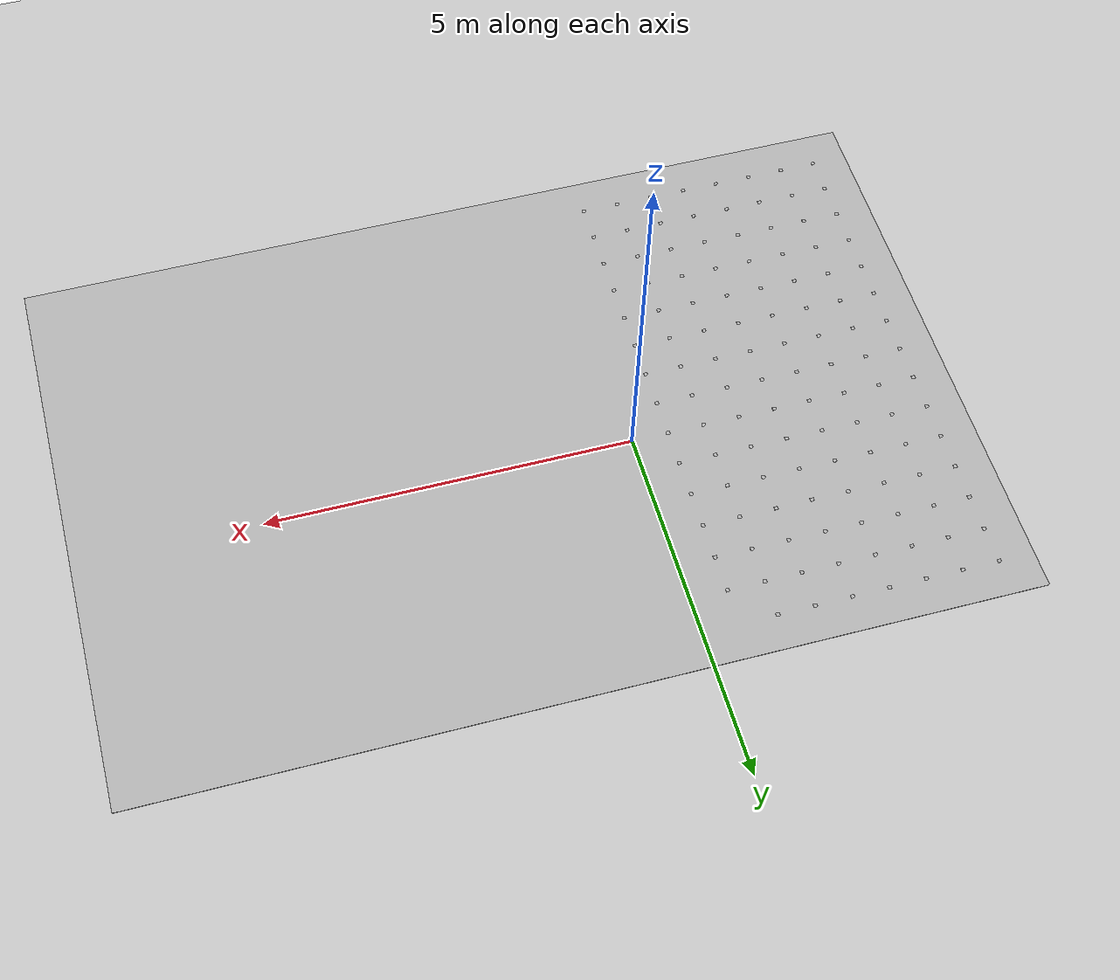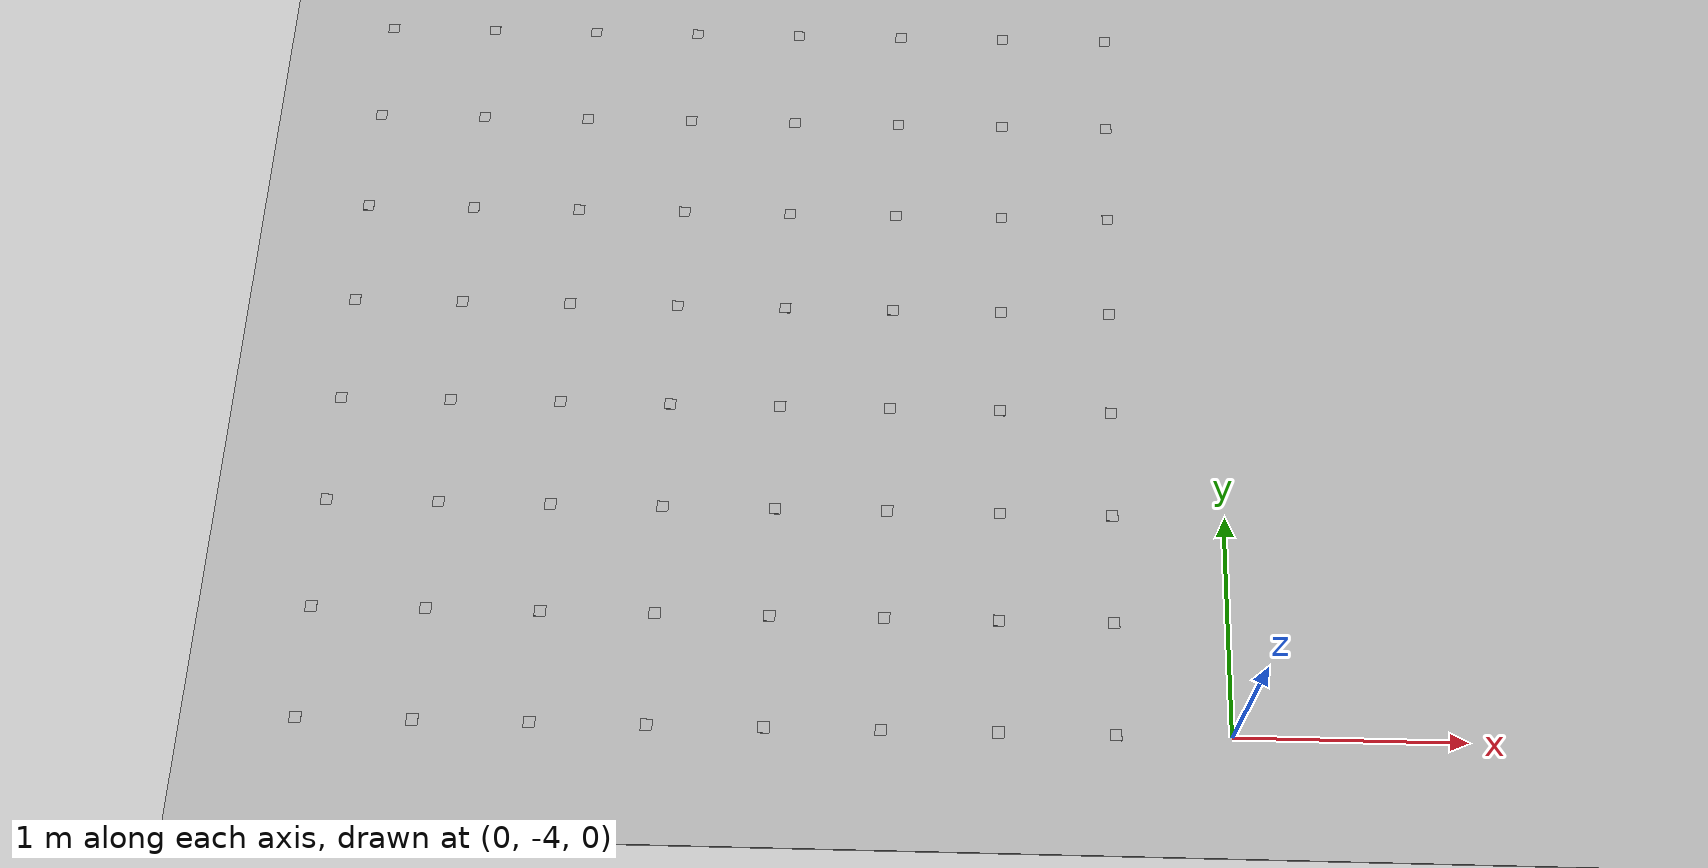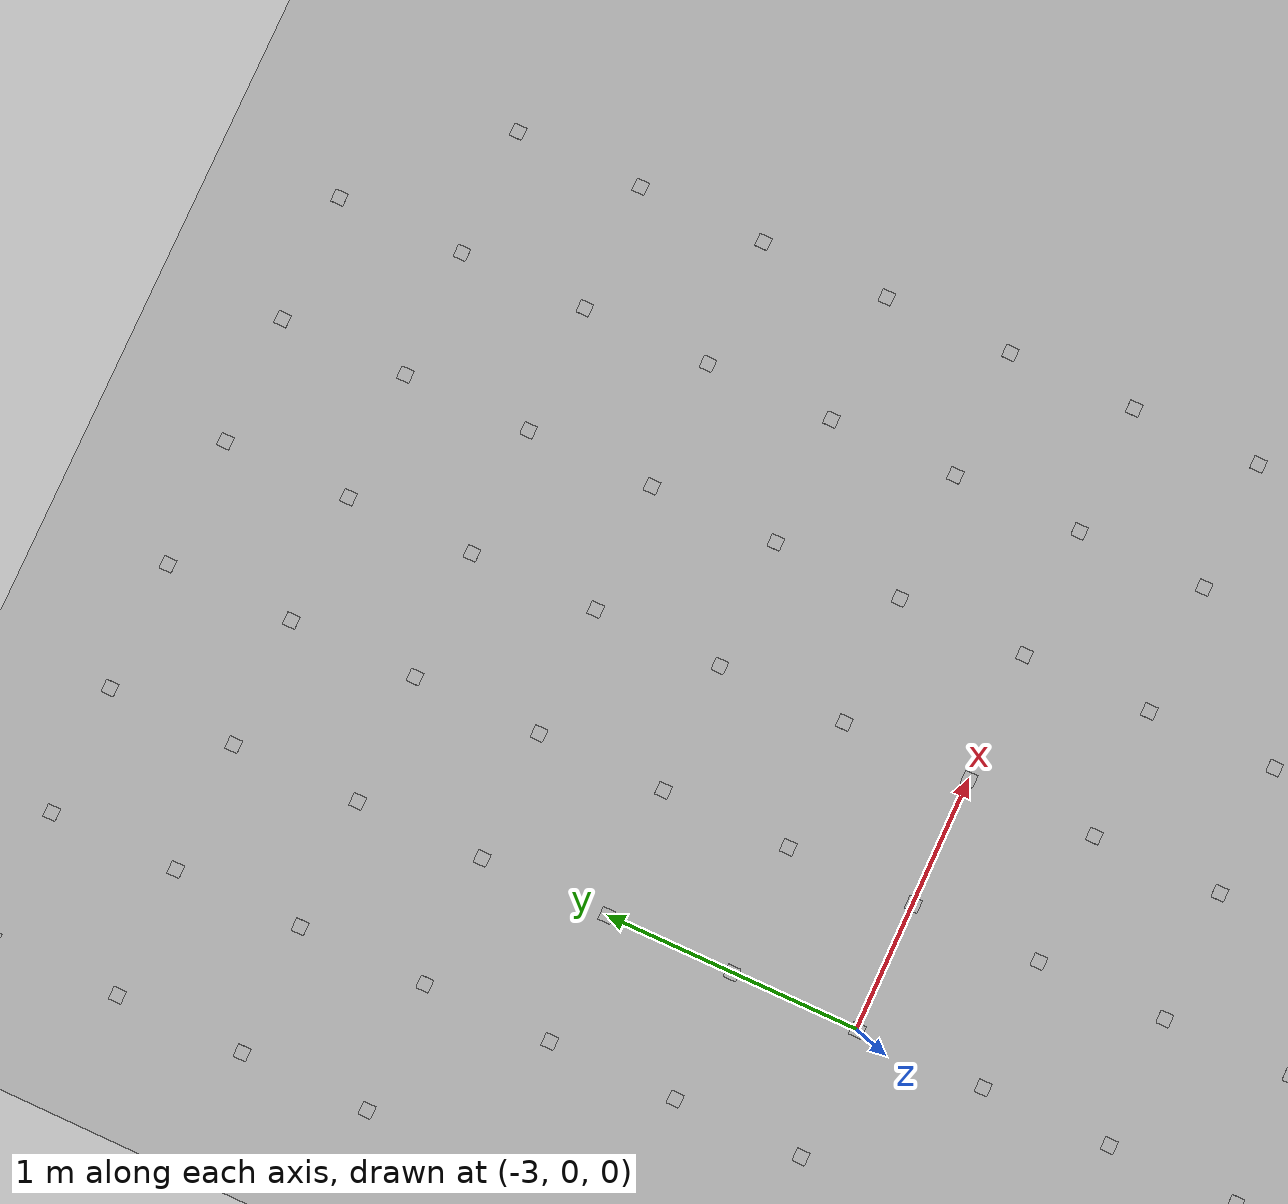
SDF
<sdf version="1.7">
 <world name="default">
  <physics name="default_physics" default="0" type="ode">
   <ode>
    <solver>
     <type>quick</type>
     <iters>10</iters>
     <sor>1.3</sor>
     <use_dynamic_moi_rescaling>0</use_dynamic_moi_rescaling>
    </solver>
    <constraints>
     <cfm>0</cfm>
     <erp>0.2</erp>
     <contact_max_correcting_vel>1000</contact_max_correcting_vel>
     <contact_surface_layer>0.001</contact_surface_layer>
    </constraints>
   </ode>
   <max_step_size>0.004</max_step_size>
   <real_time_factor>1</real_time_factor>
   <real_time_update_rate>250</real_time_update_rate>
  </physics>
  <scene><shadows>0</shadows><ambient>0.4 0.4 0.4 1</ambient><background>0.7 0.7 0.7 1</background></scene>
  <light name="sun" type="directional">
   <pose>0 0 1000 0.4 0.2 0</pose>
   <diffuse>1 1 1 1</diffuse>
   <specular>0.6 0.6 0.6 1</specular>
   <direction>0.1 0.1 -0.9</direction>
   <attenuation>
    <range>20</range>
    <constant>0.5</constant>
    <linear>0.01</linear>
    <quadratic>0.001</quadratic>
   </attenuation>
   <spot><inner_angle>0</inner_angle><outer_angle>0</outer_angle><falloff>0</falloff></spot>
  </light>
  <model name="ground_plane">
   <static>1</static>
   <link name="link">
    <collision name="collision">
     <geometry><plane><normal>0 0 1</normal><size>100 100</size></plane></geometry>
     <surface>
      <contact><collide_bitmask>65535</collide_bitmask></contact>
      <friction><ode><mu>100</mu><mu2>50</mu2></ode></friction>
     </surface>
    </collision>
    <visual name="visual">
     <cast_shadows>0</cast_shadows>
     <geometry><plane><normal>0 0 1</normal><size>100 100</size></plane></geometry>
     <material>
      <script><uri>file://media/materials/scripts/gazebo.material</uri><name>Gazebo/Grey</name></script>
     </material>
    </visual>
   </link>
  </model>
  <model name="warehouse">
   <static>1</static>
   <link name="link">
    <collision name="collision">
     <geometry><mesh><uri>model://warehouse/meshes/warehouse.dae</uri><scale>1 1 1</scale></mesh></geometry>
    </collision>
    <visual name="visual">
     <geometry><mesh><uri>model://warehouse/meshes/warehouse.dae</uri><scale>1 1 1</scale></mesh></geometry>
    </visual>
   </link>
   <pose>1.51012 -0.518801 0 0 -0 3.14</pose>
  </model>
  <model name="tag1">
   <frame name="tag1::__model__" attached_to="tag1::link">
    <pose relative_to="__model__">-4 -4 0.011 0 -0 0</pose>
   </frame>
   <static>1</static>
   <link name="tag1::link">
    <collision name="collision">
     <geometry><mesh><uri>model://tags/tag1/meshes/tag1.dae</uri></mesh></geometry>
    </collision>
    <visual name="visual"><geometry><mesh><uri>model://tags/tag1/meshes/tag1.dae</uri></mesh></geometry></visual>
    <pose relative_to="tag1::__model__">0 0 0 0 -0 0</pose>
   </link>
  </model>
  <model name="tag2">
   <frame name="tag2::__model__" attached_to="tag2::link">
    <pose relative_to="__model__">-4 -3.5 0.011 0 -0 0</pose>
   </frame>
   <static>1</static>
   <link name="tag2::link">
    <collision name="collision">
     <geometry><mesh><uri>model://tags/tag2/meshes/tag2.dae</uri></mesh></geometry>
    </collision>
    <visual name="visual"><geometry><mesh><uri>model://tags/tag2/meshes/tag2.dae</uri></mesh></geometry></visual>
    <pose relative_to="tag2::__model__">0 0 0 0 -0 0</pose>
   </link>
  </model>
  <model name="tag3">
   <frame name="tag3::__model__" attached_to="tag3::link">
    <pose relative_to="__model__">-4 -3 0.011 0 -0 0</pose>
   </frame>
   <static>1</static>
   <link name="tag3::link">
    <collision name="collision">
     <geometry><mesh><uri>model://tags/tag3/meshes/tag3.dae</uri></mesh></geometry>
    </collision>
    <visual name="visual"><geometry><mesh><uri>model://tags/tag3/meshes/tag3.dae</uri></mesh></geometry></visual>
    <pose relative_to="tag3::__model__">0 0 0 0 -0 0</pose>
   </link>
  </model>
  <model name="tag4">
   <frame name="tag4::__model__" attached_to="tag4::link">
    <pose relative_to="__model__">-4 -2.5 0.011 0 -0 0</pose>
   </frame>
   <static>1</static>
   <link name="tag4::link">
    <collision name="collision">
     <geometry><mesh><uri>model://tags/tag4/meshes/tag4.dae</uri></mesh></geometry>
    </collision>
    <visual name="visual"><geometry><mesh><uri>model://tags/tag4/meshes/tag4.dae</uri></mesh></geometry></visual>
    <pose relative_to="tag4::__model__">0 0 0 0 -0 0</pose>
   </link>
  </model>
  <model name="tag5">
   <frame name="tag5::__model__" attached_to="tag5::link">
    <pose relative_to="__model__">-4 -2 0.011 0 -0 0</pose>
   </frame>
   <static>1</static>
   <link name="tag5::link">
    <collision name="collision">
     <geometry><mesh><uri>model://tags/tag5/meshes/tag5.dae</uri></mesh></geometry>
    </collision>
    <visual name="visual"><geometry><mesh><uri>model://tags/tag5/meshes/tag5.dae</uri></mesh></geometry></visual>
    <pose relative_to="tag5::__model__">0 0 0 0 -0 0</pose>
   </link>
  </model>
  <model name="tag6">
   <frame name="tag6::__model__" attached_to="tag6::link">
    <pose relative_to="__model__">-4 -1.5 0.011 0 -0 0</pose>
   </frame>
   <static>1</static>
   <link name="tag6::link">
    <collision name="collision">
     <geometry><mesh><uri>model://tags/tag6/meshes/tag6.dae</uri></mesh></geometry>
    </collision>
    <visual name="visual"><geometry><mesh><uri>model://tags/tag6/meshes/tag6.dae</uri></mesh></geometry></visual>
    <pose relative_to="tag6::__model__">0 0 0 0 -0 0</pose>
   </link>
  </model>
  <model name="tag7">
   <frame name="tag7::__model__" attached_to="tag7::link">
    <pose relative_to="__model__">-4 -1 0.011 0 -0 0</pose>
   </frame>
   <static>1</static>
   <link name="tag7::link">
    <collision name="collision">
     <geometry><mesh><uri>model://tags/tag7/meshes/tag7.dae</uri></mesh></geometry>
    </collision>
    <visual name="visual"><geometry><mesh><uri>model://tags/tag7/meshes/tag7.dae</uri></mesh></geometry></visual>
    <pose relative_to="tag7::__model__">0 0 0 0 -0 0</pose>
   </link>
  </model>
  <model name="tag8">
   <frame name="tag8::__model__" attached_to="tag8::link">
    <pose relative_to="__model__">-4 -0.5 0.011 0 -0 0</pose>
   </frame>
   <static>1</static>
   <link name="tag8::link">
    <collision name="collision">
     <geometry><mesh><uri>model://tags/tag8/meshes/tag8.dae</uri></mesh></geometry>
    </collision>
    <visual name="visual"><geometry><mesh><uri>model://tags/tag8/meshes/tag8.dae</uri></mesh></geometry></visual>
    <pose relative_to="tag8::__model__">0 0 0 0 -0 0</pose>
   </link>
  </model>
  <model name="tag9">
   <frame name="tag9::__model__" attached_to="tag9::link">
    <pose relative_to="__model__">-4 0 0.011 0 -0 0</pose>
   </frame>
   <static>1</static>
   <link name="tag9::link">
    <collision name="collision">
     <geometry><mesh><uri>model://tags/tag9/meshes/tag9.dae</uri></mesh></geometry>
    </collision>
    <visual name="visual"><geometry><mesh><uri>model://tags/tag9/meshes/tag9.dae</uri></mesh></geometry></visual>
    <pose relative_to="tag9::__model__">0 0 0 0 -0 0</pose>
   </link>
  </model>
  <model name="tag10">
   <frame name="tag10::__model__" attached_to="tag10::link">
    <pose relative_to="__model__">-4 0.5 0.011 0 -0 0</pose>
   </frame>
   <static>1</static>
   <link name="tag10::link">
    <collision name="collision">
     <geometry><mesh><uri>model://tags/tag10/meshes/tag10.dae</uri></mesh></geometry>
    </collision>
    <visual name="visual">
     <geometry><mesh><uri>model://tags/tag10/meshes/tag10.dae</uri></mesh></geometry>
    </visual>
    <pose relative_to="tag10::__model__">0 0 0 0 -0 0</pose>
   </link>
  </model>
  <model name="tag11">
   <frame name="tag11::__model__" attached_to="tag11::link">
    <pose relative_to="__model__">-4 1 0.011 0 -0 0</pose>
   </frame>
   <static>1</static>
   <link name="tag11::link">
    <collision name="collision">
     <geometry><mesh><uri>model://tags/tag11/meshes/tag11.dae</uri></mesh></geometry>
    </collision>
    <visual name="visual">
     <geometry><mesh><uri>model://tags/tag11/meshes/tag11.dae</uri></mesh></geometry>
    </visual>
    <pose relative_to="tag11::__model__">0 0 0 0 -0 0</pose>
   </link>
  </model>
  <model name="tag12">
   <frame name="tag12::__model__" attached_to="tag12::link">
    <pose relative_to="__model__">-4 1.5 0.011 0 -0 0</pose>
   </frame>
   <static>1</static>
   <link name="tag12::link">
    <collision name="collision">
     <geometry><mesh><uri>model://tags/tag12/meshes/tag12.dae</uri></mesh></geometry>
    </collision>
    <visual name="visual">
     <geometry><mesh><uri>model://tags/tag12/meshes/tag12.dae</uri></mesh></geometry>
    </visual>
    <pose relative_to="tag12::__model__">0 0 0 0 -0 0</pose>
   </link>
  </model>
  <model name="tag13">
   <frame name="tag13::__model__" attached_to="tag13::link">
    <pose relative_to="__model__">-4 2 0.011 0 -0 0</pose>
   </frame>
   <static>1</static>
   <link name="tag13::link">
    <collision name="collision">
     <geometry><mesh><uri>model://tags/tag13/meshes/tag13.dae</uri></mesh></geometry>
    </collision>
    <visual name="visual">
     <geometry><mesh><uri>model://tags/tag13/meshes/tag13.dae</uri></mesh></geometry>
    </visual>
    <pose relative_to="tag13::__model__">0 0 0 0 -0 0</pose>
   </link>
  </model>
  <model name="tag14">
   <frame name="tag14::__model__" attached_to="tag14::link">
    <pose relative_to="__model__">-4 2.5 0.011 0 -0 0</pose>
   </frame>
   <static>1</static>
   <link name="tag14::link">
    <collision name="collision">
     <geometry><mesh><uri>model://tags/tag14/meshes/tag14.dae</uri></mesh></geometry>
    </collision>
    <visual name="visual">
     <geometry><mesh><uri>model://tags/tag14/meshes/tag14.dae</uri></mesh></geometry>
    </visual>
    <pose relative_to="tag14::__model__">0 0 0 0 -0 0</pose>
   </link>
  </model>
  <model name="tag15">
   <frame name="tag15::__model__" attached_to="tag15::link">
    <pose relative_to="__model__">-4 3 0.011 0 -0 0</pose>
   </frame>
   <static>1</static>
   <link name="tag15::link">
    <collision name="collision">
     <geometry><mesh><uri>model://tags/tag15/meshes/tag15.dae</uri></mesh></geometry>
    </collision>
    <visual name="visual">
     <geometry><mesh><uri>model://tags/tag15/meshes/tag15.dae</uri></mesh></geometry>
    </visual>
    <pose relative_to="tag15::__model__">0 0 0 0 -0 0</pose>
   </link>
  </model>
  <model name="tag16">
   <frame name="tag16::__model__" attached_to="tag16::link">
    <pose relative_to="__model__">-3.5 -4 0.011 0 -0 0</pose>
   </frame>
   <static>1</static>
   <link name="tag16::link">
    <collision name="collision">
     <geometry><mesh><uri>model://tags/tag16/meshes/tag16.dae</uri></mesh></geometry>
    </collision>
    <visual name="visual">
     <geometry><mesh><uri>model://tags/tag16/meshes/tag16.dae</uri></mesh></geometry>
    </visual>
    <pose relative_to="tag16::__model__">0 0 0 0 -0 0</pose>
   </link>
  </model>
  <model name="tag17">
   <frame name="tag17::__model__" attached_to="tag17::link">
    <pose relative_to="__model__">-3.5 -3.5 0.011 0 -0 0</pose>
   </frame>
   <static>1</static>
   <link name="tag17::link">
    <collision name="collision">
     <geometry><mesh><uri>model://tags/tag17/meshes/tag17.dae</uri></mesh></geometry>
    </collision>
    <visual name="visual">
     <geometry><mesh><uri>model://tags/tag17/meshes/tag17.dae</uri></mesh></geometry>
    </visual>
    <pose relative_to="tag17::__model__">0 0 0 0 -0 0</pose>
   </link>
  </model>
  <model name="tag18">
   <frame name="tag18::__model__" attached_to="tag18::link">
    <pose relative_to="__model__">-3.5 -3 0.011 0 -0 0</pose>
   </frame>
   <static>1</static>
   <link name="tag18::link">
    <collision name="collision">
     <geometry><mesh><uri>model://tags/tag18/meshes/tag18.dae</uri></mesh></geometry>
    </collision>
    <visual name="visual">
     <geometry><mesh><uri>model://tags/tag18/meshes/tag18.dae</uri></mesh></geometry>
    </visual>
    <pose relative_to="tag18::__model__">0 0 0 0 -0 0</pose>
   </link>
  </model>
  <model name="tag19">
   <frame name="tag19::__model__" attached_to="tag19::link">
    <pose relative_to="__model__">-3.5 -2.5 0.011 0 -0 0</pose>
   </frame>
   <static>1</static>
   <link name="tag19::link">
    <collision name="collision">
     <geometry><mesh><uri>model://tags/tag19/meshes/tag19.dae</uri></mesh></geometry>
    </collision>
    <visual name="visual">
     <geometry><mesh><uri>model://tags/tag19/meshes/tag19.dae</uri></mesh></geometry>
    </visual>
    <pose relative_to="tag19::__model__">0 0 0 0 -0 0</pose>
   </link>
  </model>
  <model name="tag20">
   <frame name="tag20::__model__" attached_to="tag20::link">
    <pose relative_to="__model__">-3.5 -2 0.011 0 -0 0</pose>
   </frame>
   <static>1</static>
   <link name="tag20::link">
    <collision name="collision">
     <geometry><mesh><uri>model://tags/tag20/meshes/tag20.dae</uri></mesh></geometry>
    </collision>
    <visual name="visual">
     <geometry><mesh><uri>model://tags/tag20/meshes/tag20.dae</uri></mesh></geometry>
    </visual>
    <pose relative_to="tag20::__model__">0 0 0 0 -0 0</pose>
   </link>
  </model>
  <model name="tag21">
   <frame name="tag21::__model__" attached_to="tag21::link">
    <pose relative_to="__model__">-3.5 -1.5 0.011 0 -0 0</pose>
   </frame>
   <static>1</static>
   <link name="tag21::link">
    <collision name="collision">
     <geometry><mesh><uri>model://tags/tag21/meshes/tag21.dae</uri></mesh></geometry>
    </collision>
    <visual name="visual">
     <geometry><mesh><uri>model://tags/tag21/meshes/tag21.dae</uri></mesh></geometry>
    </visual>
    <pose relative_to="tag21::__model__">0 0 0 0 -0 0</pose>
   </link>
  </model>
  <model name="tag22">
   <frame name="tag22::__model__" attached_to="tag22::link">
    <pose relative_to="__model__">-3.5 -1 0.011 0 -0 0</pose>
   </frame>
   <static>1</static>
   <link name="tag22::link">
    <collision name="collision">
     <geometry><mesh><uri>model://tags/tag22/meshes/tag22.dae</uri></mesh></geometry>
    </collision>
    <visual name="visual">
     <geometry><mesh><uri>model://tags/tag22/meshes/tag22.dae</uri></mesh></geometry>
    </visual>
    <pose relative_to="tag22::__model__">0 0 0 0 -0 0</pose>
   </link>
  </model>
  <model name="tag23">
   <frame name="tag23::__model__" attached_to="tag23::link">
    <pose relative_to="__model__">-3.5 -0.5 0.011 0 -0 0</pose>
   </frame>
   <static>1</static>
   <link name="tag23::link">
    <collision name="collision">
     <geometry><mesh><uri>model://tags/tag23/meshes/tag23.dae</uri></mesh></geometry>
    </collision>
    <visual name="visual">
     <geometry><mesh><uri>model://tags/tag23/meshes/tag23.dae</uri></mesh></geometry>
    </visual>
    <pose relative_to="tag23::__model__">0 0 0 0 -0 0</pose>
   </link>
  </model>
  <model name="tag24">
   <frame name="tag24::__model__" attached_to="tag24::link">
    <pose relative_to="__model__">-3.5 0 0.011 0 -0 0</pose>
   </frame>
   <static>1</static>
   <link name="tag24::link">
    <collision name="collision">
     <geometry><mesh><uri>model://tags/tag24/meshes/tag24.dae</uri></mesh></geometry>
    </collision>
    <visual name="visual">
     <geometry><mesh><uri>model://tags/tag24/meshes/tag24.dae</uri></mesh></geometry>
    </visual>
    <pose relative_to="tag24::__model__">0 0 0 0 -0 0</pose>
   </link>
  </model>
  <model name="tag25">
   <frame name="tag25::__model__" attached_to="tag25::link">
    <pose relative_to="__model__">-3.5 0.5 0.011 0 -0 0</pose>
   </frame>
   <static>1</static>
   <link name="tag25::link">
    <collision name="collision">
     <geometry><mesh><uri>model://tags/tag25/meshes/tag25.dae</uri></mesh></geometry>
    </collision>
    <visual name="visual">
     <geometry><mesh><uri>model://tags/tag25/meshes/tag25.dae</uri></mesh></geometry>
    </visual>
    <pose relative_to="tag25::__model__">0 0 0 0 -0 0</pose>
   </link>
  </model>
  <model name="tag26">
   <frame name="tag26::__model__" attached_to="tag26::link">
    <pose relative_to="__model__">-3.5 1 0.011 0 -0 0</pose>
   </frame>
   <static>1</static>
   <link name="tag26::link">
    <collision name="collision">
     <geometry><mesh><uri>model://tags/tag26/meshes/tag26.dae</uri></mesh></geometry>
    </collision>
    <visual name="visual">
     <geometry><mesh><uri>model://tags/tag26/meshes/tag26.dae</uri></mesh></geometry>
    </visual>
    <pose relative_to="tag26::__model__">0 0 0 0 -0 0</pose>
   </link>
  </model>
  <model name="tag27">
   <frame name="tag27::__model__" attached_to="tag27::link">
    <pose relative_to="__model__">-3.5 1.5 0.011 0 -0 0</pose>
   </frame>
   <static>1</static>
   <link name="tag27::link">
    <collision name="collision">
     <geometry><mesh><uri>model://tags/tag27/meshes/tag27.dae</uri></mesh></geometry>
    </collision>
    <visual name="visual">
     <geometry><mesh><uri>model://tags/tag27/meshes/tag27.dae</uri></mesh></geometry>
    </visual>
    <pose relative_to="tag27::__model__">0 0 0 0 -0 0</pose>
   </link>
  </model>
  <model name="tag28">
   <frame name="tag28::__model__" attached_to="tag28::link">
    <pose relative_to="__model__">-3.5 2 0.011 0 -0 0</pose>
   </frame>
   <static>1</static>
   <link name="tag28::link">
    <collision name="collision">
     <geometry><mesh><uri>model://tags/tag28/meshes/tag28.dae</uri></mesh></geometry>
    </collision>
    <visual name="visual">
     <geometry><mesh><uri>model://tags/tag28/meshes/tag28.dae</uri></mesh></geometry>
    </visual>
    <pose relative_to="tag28::__model__">0 0 0 0 -0 0</pose>
   </link>
  </model>
  <model name="tag29">
   <frame name="tag29::__model__" attached_to="tag29::link">
    <pose relative_to="__model__">-3.5 2.5 0.011 0 -0 0</pose>
   </frame>
   <static>1</static>
   <link name="tag29::link">
    <collision name="collision">
     <geometry><mesh><uri>model://tags/tag29/meshes/tag29.dae</uri></mesh></geometry>
    </collision>
    <visual name="visual">
     <geometry><mesh><uri>model://tags/tag29/meshes/tag29.dae</uri></mesh></geometry>
    </visual>
    <pose relative_to="tag29::__model__">0 0 0 0 -0 0</pose>
   </link>
  </model>
  <model name="tag30">
   <frame name="tag30::__model__" attached_to="tag30::link">
    <pose relative_to="__model__">-3.5 3 0.011 0 -0 0</pose>
   </frame>
   <static>1</static>
   <link name="tag30::link">
    <collision name="collision">
     <geometry><mesh><uri>model://tags/tag30/meshes/tag30.dae</uri></mesh></geometry>
    </collision>
    <visual name="visual">
     <geometry><mesh><uri>model://tags/tag30/meshes/tag30.dae</uri></mesh></geometry>
    </visual>
    <pose relative_to="tag30::__model__">0 0 0 0 -0 0</pose>
   </link>
  </model>
  <model name="tag31">
   <frame name="tag31::__model__" attached_to="tag31::link">
    <pose relative_to="__model__">-3 -4 0.011 0 -0 0</pose>
   </frame>
   <static>1</static>
   <link name="tag31::link">
    <collision name="collision">
     <geometry><mesh><uri>model://tags/tag31/meshes/tag31.dae</uri></mesh></geometry>
    </collision>
    <visual name="visual">
     <geometry><mesh><uri>model://tags/tag31/meshes/tag31.dae</uri></mesh></geometry>
    </visual>
    <pose relative_to="tag31::__model__">0 0 0 0 -0 0</pose>
   </link>
  </model>
  <model name="tag32">
   <frame name="tag32::__model__" attached_to="tag32::link">
    <pose relative_to="__model__">-3 -3.5 0.011 0 -0 0</pose>
   </frame>
   <static>1</static>
   <link name="tag32::link">
    <collision name="collision">
     <geometry><mesh><uri>model://tags/tag32/meshes/tag32.dae</uri></mesh></geometry>
    </collision>
    <visual name="visual">
     <geometry><mesh><uri>model://tags/tag32/meshes/tag32.dae</uri></mesh></geometry>
    </visual>
    <pose relative_to="tag32::__model__">0 0 0 0 -0 0</pose>
   </link>
  </model>
  <model name="tag33">
   <frame name="tag33::__model__" attached_to="tag33::link">
    <pose relative_to="__model__">-3 -3 0.011 0 -0 0</pose>
   </frame>
   <static>1</static>
   <link name="tag33::link">
    <collision name="collision">
     <geometry><mesh><uri>model://tags/tag33/meshes/tag33.dae</uri></mesh></geometry>
    </collision>
    <visual name="visual">
     <geometry><mesh><uri>model://tags/tag33/meshes/tag33.dae</uri></mesh></geometry>
    </visual>
    <pose relative_to="tag33::__model__">0 0 0 0 -0 0</pose>
   </link>
  </model>
  <model name="tag34">
   <frame name="tag34::__model__" attached_to="tag34::link">
    <pose relative_to="__model__">-3 -2.5 0.011 0 -0 0</pose>
   </frame>
   <static>1</static>
   <link name="tag34::link">
    <collision name="collision">
     <geometry><mesh><uri>model://tags/tag34/meshes/tag34.dae</uri></mesh></geometry>
    </collision>
    <visual name="visual">
     <geometry><mesh><uri>model://tags/tag34/meshes/tag34.dae</uri></mesh></geometry>
    </visual>
    <pose relative_to="tag34::__model__">0 0 0 0 -0 0</pose>
   </link>
  </model>
  <model name="tag35">
   <frame name="tag35::__model__" attached_to="tag35::link">
    <pose relative_to="__model__">-3 -2 0.011 0 -0 0</pose>
   </frame>
   <static>1</static>
   <link name="tag35::link">
    <collision name="collision">
     <geometry><mesh><uri>model://tags/tag35/meshes/tag35.dae</uri></mesh></geometry>
    </collision>
    <visual name="visual">
     <geometry><mesh><uri>model://tags/tag35/meshes/tag35.dae</uri></mesh></geometry>
    </visual>
    <pose relative_to="tag35::__model__">0 0 0 0 -0 0</pose>
   </link>
  </model>
  <model name="tag36">
   <frame name="tag36::__model__" attached_to="tag36::link">
    <pose relative_to="__model__">-3 -1.5 0.011 0 -0 0</pose>
   </frame>
   <static>1</static>
   <link name="tag36::link">
    <collision name="collision">
     <geometry><mesh><uri>model://tags/tag36/meshes/tag36.dae</uri></mesh></geometry>
    </collision>
    <visual name="visual">
     <geometry><mesh><uri>model://tags/tag36/meshes/tag36.dae</uri></mesh></geometry>
    </visual>
    <pose relative_to="tag36::__model__">0 0 0 0 -0 0</pose>
   </link>
  </model>
  <model name="tag37">
   <frame name="tag37::__model__" attached_to="tag37::link">
    <pose relative_to="__model__">-3 -1 0.011 0 -0 0</pose>
   </frame>
   <static>1</static>
   <link name="tag37::link">
    <collision name="collision">
     <geometry><mesh><uri>model://tags/tag37/meshes/tag37.dae</uri></mesh></geometry>
    </collision>
    <visual name="visual">
     <geometry><mesh><uri>model://tags/tag37/meshes/tag37.dae</uri></mesh></geometry>
    </visual>
    <pose relative_to="tag37::__model__">0 0 0 0 -0 0</pose>
   </link>
  </model>
  <model name="tag38">
   <frame name="tag38::__model__" attached_to="tag38::link">
    <pose relative_to="__model__">-3 -0.5 0.011 0 -0 0</pose>
   </frame>
   <static>1</static>
   <link name="tag38::link">
    <collision name="collision">
     <geometry><mesh><uri>model://tags/tag38/meshes/tag38.dae</uri></mesh></geometry>
    </collision>
    <visual name="visual">
     <geometry><mesh><uri>model://tags/tag38/meshes/tag38.dae</uri></mesh></geometry>
    </visual>
    <pose relative_to="tag38::__model__">0 0 0 0 -0 0</pose>
   </link>
  </model>
  <model name="tag39">
   <frame name="tag39::__model__" attached_to="tag39::link">
    <pose relative_to="__model__">-3 0 0.011 0 -0 0</pose>
   </frame>
   <static>1</static>
   <link name="tag39::link">
    <collision name="collision">
     <geometry><mesh><uri>model://tags/tag39/meshes/tag39.dae</uri></mesh></geometry>
    </collision>
    <visual name="visual">
     <geometry><mesh><uri>model://tags/tag39/meshes/tag39.dae</uri></mesh></geometry>
    </visual>
    <pose relative_to="tag39::__model__">0 0 0 0 -0 0</pose>
   </link>
  </model>
  <model name="tag40">
   <frame name="tag40::__model__" attached_to="tag40::link">
    <pose relative_to="__model__">-3 0.5 0.011 0 -0 0</pose>
   </frame>
   <static>1</static>
   <link name="tag40::link">
    <collision name="collision">
     <geometry><mesh><uri>model://tags/tag40/meshes/tag40.dae</uri></mesh></geometry>
    </collision>
    <visual name="visual">
     <geometry><mesh><uri>model://tags/tag40/meshes/tag40.dae</uri></mesh></geometry>
    </visual>
    <pose relative_to="tag40::__model__">0 0 0 0 -0 0</pose>
   </link>
  </model>
  <model name="tag41">
   <frame name="tag41::__model__" attached_to="tag41::link">
    <pose relative_to="__model__">-3 1 0.011 0 -0 0</pose>
   </frame>
   <static>1</static>
   <link name="tag41::link">
    <collision name="collision">
     <geometry><mesh><uri>model://tags/tag41/meshes/tag41.dae</uri></mesh></geometry>
    </collision>
    <visual name="visual">
     <geometry><mesh><uri>model://tags/tag41/meshes/tag41.dae</uri></mesh></geometry>
    </visual>
    <pose relative_to="tag41::__model__">0 0 0 0 -0 0</pose>
   </link>
  </model>
  <model name="tag42">
   <frame name="tag42::__model__" attached_to="tag42::link">
    <pose relative_to="__model__">-3 1.5 0.011 0 -0 0</pose>
   </frame>
   <static>1</static>
   <link name="tag42::link">
    <collision name="collision">
     <geometry><mesh><uri>model://tags/tag42/meshes/tag42.dae</uri></mesh></geometry>
    </collision>
    <visual name="visual">
     <geometry><mesh><uri>model://tags/tag42/meshes/tag42.dae</uri></mesh></geometry>
    </visual>
    <pose relative_to="tag42::__model__">0 0 0 0 -0 0</pose>
   </link>
  </model>
  <model name="tag43">
   <frame name="tag43::__model__" attached_to="tag43::link">
    <pose relative_to="__model__">-3 2 0.011 0 -0 0</pose>
   </frame>
   <static>1</static>
   <link name="tag43::link">
    <collision name="collision">
     <geometry><mesh><uri>model://tags/tag43/meshes/tag43.dae</uri></mesh></geometry>
    </collision>
    <visual name="visual">
     <geometry><mesh><uri>model://tags/tag43/meshes/tag43.dae</uri></mesh></geometry>
    </visual>
    <pose relative_to="tag43::__model__">0 0 0 0 -0 0</pose>
   </link>
  </model>
  <model name="tag44">
   <frame name="tag44::__model__" attached_to="tag44::link">
    <pose relative_to="__model__">-3 2.5 0.011 0 -0 0</pose>
   </frame>
   <static>1</static>
   <link name="tag44::link">
    <collision name="collision">
     <geometry><mesh><uri>model://tags/tag44/meshes/tag44.dae</uri></mesh></geometry>
    </collision>
    <visual name="visual">
     <geometry><mesh><uri>model://tags/tag44/meshes/tag44.dae</uri></mesh></geometry>
    </visual>
    <pose relative_to="tag44::__model__">0 0 0 0 -0 0</pose>
   </link>
  </model>
  <model name="tag45">
   <frame name="tag45::__model__" attached_to="tag45::link">
    <pose relative_to="__model__">-3 3 0.011 0 -0 0</pose>
   </frame>
   <static>1</static>
   <link name="tag45::link">
    <collision name="collision">
     <geometry><mesh><uri>model://tags/tag45/meshes/tag45.dae</uri></mesh></geometry>
    </collision>
    <visual name="visual">
     <geometry><mesh><uri>model://tags/tag45/meshes/tag45.dae</uri></mesh></geometry>
    </visual>
    <pose relative_to="tag45::__model__">0 0 0 0 -0 0</pose>
   </link>
  </model>
  <model name="tag46">
   <frame name="tag46::__model__" attached_to="tag46::link">
    <pose relative_to="__model__">-2.5 -4 0.011 0 -0 0</pose>
   </frame>
   <static>1</static>
   <link name="tag46::link">
    <collision name="collision">
     <geometry><mesh><uri>model://tags/tag46/meshes/tag46.dae</uri></mesh></geometry>
    </collision>
    <visual name="visual">
     <geometry><mesh><uri>model://tags/tag46/meshes/tag46.dae</uri></mesh></geometry>
    </visual>
    <pose relative_to="tag46::__model__">0 0 0 0 -0 0</pose>
   </link>
  </model>
  <model name="tag47">
   <frame name="tag47::__model__" attached_to="tag47::link">
    <pose relative_to="__model__">-2.5 -3.5 0.011 0 -0 0</pose>
   </frame>
   <static>1</static>
   <link name="tag47::link">
    <collision name="collision">
     <geometry><mesh><uri>model://tags/tag47/meshes/tag47.dae</uri></mesh></geometry>
    </collision>
    <visual name="visual">
     <geometry><mesh><uri>model://tags/tag47/meshes/tag47.dae</uri></mesh></geometry>
    </visual>
    <pose relative_to="tag47::__model__">0 0 0 0 -0 0</pose>
   </link>
  </model>
  <model name="tag48">
   <frame name="tag48::__model__" attached_to="tag48::link">
    <pose relative_to="__model__">-2.5 -3 0.011 0 -0 0</pose>
   </frame>
   <static>1</static>
   <link name="tag48::link">
    <collision name="collision">
     <geometry><mesh><uri>model://tags/tag48/meshes/tag48.dae</uri></mesh></geometry>
    </collision>
    <visual name="visual">
     <geometry><mesh><uri>model://tags/tag48/meshes/tag48.dae</uri></mesh></geometry>
    </visual>
    <pose relative_to="tag48::__model__">0 0 0 0 -0 0</pose>
   </link>
  </model>
  <model name="tag49">
   <frame name="tag49::__model__" attached_to="tag49::link">
    <pose relative_to="__model__">-2.5 -2.5 0.011 0 -0 0</pose>
   </frame>
   <static>1</static>
   <link name="tag49::link">
    <collision name="collision">
     <geometry><mesh><uri>model://tags/tag49/meshes/tag49.dae</uri></mesh></geometry>
    </collision>
    <visual name="visual">
     <geometry><mesh><uri>model://tags/tag49/meshes/tag49.dae</uri></mesh></geometry>
    </visual>
    <pose relative_to="tag49::__model__">0 0 0 0 -0 0</pose>
   </link>
  </model>
  <model name="tag50">
   <frame name="tag50::__model__" attached_to="tag50::link">
    <pose relative_to="__model__">-2.5 -2 0.011 0 -0 0</pose>
   </frame>
   <static>1</static>
   <link name="tag50::link">
    <collision name="collision">
     <geometry><mesh><uri>model://tags/tag50/meshes/tag50.dae</uri></mesh></geometry>
    </collision>
    <visual name="visual">
     <geometry><mesh><uri>model://tags/tag50/meshes/tag50.dae</uri></mesh></geometry>
    </visual>
    <pose relative_to="tag50::__model__">0 0 0 0 -0 0</pose>
   </link>
  </model>
  <model name="tag51">
   <frame name="tag51::__model__" attached_to="tag51::link">
    <pose relative_to="__model__">-2.5 -1.5 0.011 0 -0 0</pose>
   </frame>
   <static>1</static>
   <link name="tag51::link">
    <collision name="collision">
     <geometry><mesh><uri>model://tags/tag51/meshes/tag51.dae</uri></mesh></geometry>
    </collision>
    <visual name="visual">
     <geometry><mesh><uri>model://tags/tag51/meshes/tag51.dae</uri></mesh></geometry>
    </visual>
    <pose relative_to="tag51::__model__">0 0 0 0 -0 0</pose>
   </link>
  </model>
  <model name="tag52">
   <frame name="tag52::__model__" attached_to="tag52::link">
    <pose relative_to="__model__">-2.5 -1 0.011 0 -0 0</pose>
   </frame>
   <static>1</static>
   <link name="tag52::link">
    <collision name="collision">
     <geometry><mesh><uri>model://tags/tag52/meshes/tag52.dae</uri></mesh></geometry>
    </collision>
    <visual name="visual">
     <geometry><mesh><uri>model://tags/tag52/meshes/tag52.dae</uri></mesh></geometry>
    </visual>
    <pose relative_to="tag52::__model__">0 0 0 0 -0 0</pose>
   </link>
  </model>
  <model name="tag53">
   <frame name="tag53::__model__" attached_to="tag53::link">
    <pose relative_to="__model__">-2.5 -0.5 0.011 0 -0 0</pose>
   </frame>
   <static>1</static>
   <link name="tag53::link">
    <collision name="collision">
     <geometry><mesh><uri>model://tags/tag53/meshes/tag53.dae</uri></mesh></geometry>
    </collision>
    <visual name="visual">
     <geometry><mesh><uri>model://tags/tag53/meshes/tag53.dae</uri></mesh></geometry>
    </visual>
    <pose relative_to="tag53::__model__">0 0 0 0 -0 0</pose>
   </link>
  </model>
  <model name="tag54">
   <frame name="tag54::__model__" attached_to="tag54::link">
    <pose relative_to="__model__">-2.5 0 0.011 0 -0 0</pose>
   </frame>
   <static>1</static>
   <link name="tag54::link">
    <collision name="collision">
     <geometry><mesh><uri>model://tags/tag54/meshes/tag54.dae</uri></mesh></geometry>
    </collision>
    <visual name="visual">
     <geometry><mesh><uri>model://tags/tag54/meshes/tag54.dae</uri></mesh></geometry>
    </visual>
    <pose relative_to="tag54::__model__">0 0 0 0 -0 0</pose>
   </link>
  </model>
  <model name="tag55">
   <frame name="tag55::__model__" attached_to="tag55::link">
    <pose relative_to="__model__">-2.5 0.5 0.011 0 -0 0</pose>
   </frame>
   <static>1</static>
   <link name="tag55::link">
    <collision name="collision">
     <geometry><mesh><uri>model://tags/tag55/meshes/tag55.dae</uri></mesh></geometry>
    </collision>
    <visual name="visual">
     <geometry><mesh><uri>model://tags/tag55/meshes/tag55.dae</uri></mesh></geometry>
    </visual>
    <pose relative_to="tag55::__model__">0 0 0 0 -0 0</pose>
   </link>
  </model>
  <model name="tag56">
   <frame name="tag56::__model__" attached_to="tag56::link">
    <pose relative_to="__model__">-2.5 1 0.011 0 -0 0</pose>
   </frame>
   <static>1</static>
   <link name="tag56::link">
    <collision name="collision">
     <geometry><mesh><uri>model://tags/tag56/meshes/tag56.dae</uri></mesh></geometry>
    </collision>
    <visual name="visual">
     <geometry><mesh><uri>model://tags/tag56/meshes/tag56.dae</uri></mesh></geometry>
    </visual>
    <pose relative_to="tag56::__model__">0 0 0 0 -0 0</pose>
   </link>
  </model>
  <model name="tag57">
   <frame name="tag57::__model__" attached_to="tag57::link">
    <pose relative_to="__model__">-2.5 1.5 0.011 0 -0 0</pose>
   </frame>
   <static>1</static>
   <link name="tag57::link">
    <collision name="collision">
     <geometry><mesh><uri>model://tags/tag57/meshes/tag57.dae</uri></mesh></geometry>
    </collision>
    <visual name="visual">
     <geometry><mesh><uri>model://tags/tag57/meshes/tag57.dae</uri></mesh></geometry>
    </visual>
    <pose relative_to="tag57::__model__">0 0 0 0 -0 0</pose>
   </link>
  </model>
  <model name="tag58">
   <frame name="tag58::__model__" attached_to="tag58::link">
    <pose relative_to="__model__">-2.5 2 0.011 0 -0 0</pose>
   </frame>
   <static>1</static>
   <link name="tag58::link">
    <collision name="collision">
     <geometry><mesh><uri>model://tags/tag58/meshes/tag58.dae</uri></mesh></geometry>
    </collision>
    <visual name="visual">
     <geometry><mesh><uri>model://tags/tag58/meshes/tag58.dae</uri></mesh></geometry>
    </visual>
    <pose relative_to="tag58::__model__">0 0 0 0 -0 0</pose>
   </link>
  </model>
  <model name="tag59">
   <frame name="tag59::__model__" attached_to="tag59::link">
    <pose relative_to="__model__">-2.5 2.5 0.011 0 -0 0</pose>
   </frame>
   <static>1</static>
   <link name="tag59::link">
    <collision name="collision">
     <geometry><mesh><uri>model://tags/tag59/meshes/tag59.dae</uri></mesh></geometry>
    </collision>
    <visual name="visual">
     <geometry><mesh><uri>model://tags/tag59/meshes/tag59.dae</uri></mesh></geometry>
    </visual>
    <pose relative_to="tag59::__model__">0 0 0 0 -0 0</pose>
   </link>
  </model>
  <model name="tag60">
   <frame name="tag60::__model__" attached_to="tag60::link">
    <pose relative_to="__model__">-2.5 3 0.011 0 -0 0</pose>
   </frame>
   <static>1</static>
   <link name="tag60::link">
    <collision name="collision">
     <geometry><mesh><uri>model://tags/tag60/meshes/tag60.dae</uri></mesh></geometry>
    </collision>
    <visual name="visual">
     <geometry><mesh><uri>model://tags/tag60/meshes/tag60.dae</uri></mesh></geometry>
    </visual>
    <pose relative_to="tag60::__model__">0 0 0 0 -0 0</pose>
   </link>
  </model>
  <model name="tag61">
   <frame name="tag61::__model__" attached_to="tag61::link">
    <pose relative_to="__model__">-2 -4 0.011 0 -0 0</pose>
   </frame>
   <static>1</static>
   <link name="tag61::link">
    <collision name="collision">
     <geometry><mesh><uri>model://tags/tag61/meshes/tag61.dae</uri></mesh></geometry>
    </collision>
    <visual name="visual">
     <geometry><mesh><uri>model://tags/tag61/meshes/tag61.dae</uri></mesh></geometry>
    </visual>
    <pose relative_to="tag61::__model__">0 0 0 0 -0 0</pose>
   </link>
  </model>
  <model name="tag62">
   <frame name="tag62::__model__" attached_to="tag62::link">
    <pose relative_to="__model__">-2 -3.5 0.011 0 -0 0</pose>
   </frame>
   <static>1</static>
   <link name="tag62::link">
    <collision name="collision">
     <geometry><mesh><uri>model://tags/tag62/meshes/tag62.dae</uri></mesh></geometry>
    </collision>
    <visual name="visual">
     <geometry><mesh><uri>model://tags/tag62/meshes/tag62.dae</uri></mesh></geometry>
    </visual>
    <pose relative_to="tag62::__model__">0 0 0 0 -0 0</pose>
   </link>
  </model>
  <model name="tag63">
   <frame name="tag63::__model__" attached_to="tag63::link">
    <pose relative_to="__model__">-2 -3 0.011 0 -0 0</pose>
   </frame>
   <static>1</static>
   <link name="tag63::link">
    <collision name="collision">
     <geometry><mesh><uri>model://tags/tag63/meshes/tag63.dae</uri></mesh></geometry>
    </collision>
    <visual name="visual">
     <geometry><mesh><uri>model://tags/tag63/meshes/tag63.dae</uri></mesh></geometry>
    </visual>
    <pose relative_to="tag63::__model__">0 0 0 0 -0 0</pose>
   </link>
  </model>
  <model name="tag64">
   <frame name="tag64::__model__" attached_to="tag64::link">
    <pose relative_to="__model__">-2 -2.5 0.011 0 -0 0</pose>
   </frame>
   <static>1</static>
   <link name="tag64::link">
    <collision name="collision">
     <geometry><mesh><uri>model://tags/tag64/meshes/tag64.dae</uri></mesh></geometry>
    </collision>
    <visual name="visual">
     <geometry><mesh><uri>model://tags/tag64/meshes/tag64.dae</uri></mesh></geometry>
    </visual>
    <pose relative_to="tag64::__model__">0 0 0 0 -0 0</pose>
   </link>
  </model>
  <model name="tag65">
   <frame name="tag65::__model__" attached_to="tag65::link">
    <pose relative_to="__model__">-2 -2 0.011 0 -0 0</pose>
   </frame>
   <static>1</static>
   <link name="tag65::link">
    <collision name="collision">
     <geometry><mesh><uri>model://tags/tag65/meshes/tag65.dae</uri></mesh></geometry>
    </collision>
    <visual name="visual">
     <geometry><mesh><uri>model://tags/tag65/meshes/tag65.dae</uri></mesh></geometry>
    </visual>
    <pose relative_to="tag65::__model__">0 0 0 0 -0 0</pose>
   </link>
  </model>
  <model name="tag66">
   <frame name="tag66::__model__" attached_to="tag66::link">
    <pose relative_to="__model__">-2 -1.5 0.011 0 -0 0</pose>
   </frame>
   <static>1</static>
   <link name="tag66::link">
    <collision name="collision">
     <geometry><mesh><uri>model://tags/tag66/meshes/tag66.dae</uri></mesh></geometry>
    </collision>
    <visual name="visual">
     <geometry><mesh><uri>model://tags/tag66/meshes/tag66.dae</uri></mesh></geometry>
    </visual>
    <pose relative_to="tag66::__model__">0 0 0 0 -0 0</pose>
   </link>
  </model>
  <model name="tag67">
   <frame name="tag67::__model__" attached_to="tag67::link">
    <pose relative_to="__model__">-2 -1 0.011 0 -0 0</pose>
   </frame>
   <static>1</static>
   <link name="tag67::link">
    <collision name="collision">
     <geometry><mesh><uri>model://tags/tag67/meshes/tag67.dae</uri></mesh></geometry>
    </collision>
    <visual name="visual">
     <geometry><mesh><uri>model://tags/tag67/meshes/tag67.dae</uri></mesh></geometry>
    </visual>
    <pose relative_to="tag67::__model__">0 0 0 0 -0 0</pose>
   </link>
  </model>
  <model name="tag68">
   <frame name="tag68::__model__" attached_to="tag68::link">
    <pose relative_to="__model__">-2 -0.5 0.011 0 -0 0</pose>
   </frame>
   <static>1</static>
   <link name="tag68::link">
    <collision name="collision">
     <geometry><mesh><uri>model://tags/tag68/meshes/tag68.dae</uri></mesh></geometry>
    </collision>
    <visual name="visual">
     <geometry><mesh><uri>model://tags/tag68/meshes/tag68.dae</uri></mesh></geometry>
    </visual>
    <pose relative_to="tag68::__model__">0 0 0 0 -0 0</pose>
   </link>
  </model>
  <model name="tag69">
   <frame name="tag69::__model__" attached_to="tag69::link">
    <pose relative_to="__model__">-2 0 0.011 0 -0 0</pose>
   </frame>
   <static>1</static>
   <link name="tag69::link">
    <collision name="collision">
     <geometry><mesh><uri>model://tags/tag69/meshes/tag69.dae</uri></mesh></geometry>
    </collision>
    <visual name="visual">
     <geometry><mesh><uri>model://tags/tag69/meshes/tag69.dae</uri></mesh></geometry>
    </visual>
    <pose relative_to="tag69::__model__">0 0 0 0 -0 0</pose>
   </link>
  </model>
  <model name="tag70">
   <frame name="tag70::__model__" attached_to="tag70::link">
    <pose relative_to="__model__">-2 0.5 0.011 0 -0 0</pose>
   </frame>
   <static>1</static>
   <link name="tag70::link">
    <collision name="collision">
     <geometry><mesh><uri>model://tags/tag70/meshes/tag70.dae</uri></mesh></geometry>
    </collision>
    <visual name="visual">
     <geometry><mesh><uri>model://tags/tag70/meshes/tag70.dae</uri></mesh></geometry>
    </visual>
    <pose relative_to="tag70::__model__">0 0 0 0 -0 0</pose>
   </link>
  </model>
  <model name="tag71">
   <frame name="tag71::__model__" attached_to="tag71::link">
    <pose relative_to="__model__">-2 1 0.011 0 -0 0</pose>
   </frame>
   <static>1</static>
   <link name="tag71::link">
    <collision name="collision">
     <geometry><mesh><uri>model://tags/tag71/meshes/tag71.dae</uri></mesh></geometry>
    </collision>
    <visual name="visual">
     <geometry><mesh><uri>model://tags/tag71/meshes/tag71.dae</uri></mesh></geometry>
    </visual>
    <pose relative_to="tag71::__model__">0 0 0 0 -0 0</pose>
   </link>
  </model>
  <model name="tag72">
   <frame name="tag72::__model__" attached_to="tag72::link">
    <pose relative_to="__model__">-2 1.5 0.011 0 -0 0</pose>
   </frame>
   <static>1</static>
   <link name="tag72::link">
    <collision name="collision">
     <geometry><mesh><uri>model://tags/tag72/meshes/tag72.dae</uri></mesh></geometry>
    </collision>
    <visual name="visual">
     <geometry><mesh><uri>model://tags/tag72/meshes/tag72.dae</uri></mesh></geometry>
    </visual>
    <pose relative_to="tag72::__model__">0 0 0 0 -0 0</pose>
   </link>
  </model>
  <model name="tag73">
   <frame name="tag73::__model__" attached_to="tag73::link">
    <pose relative_to="__model__">-2 2 0.011 0 -0 0</pose>
   </frame>
   <static>1</static>
   <link name="tag73::link">
    <collision name="collision">
     <geometry><mesh><uri>model://tags/tag73/meshes/tag73.dae</uri></mesh></geometry>
    </collision>
    <visual name="visual">
     <geometry><mesh><uri>model://tags/tag73/meshes/tag73.dae</uri></mesh></geometry>
    </visual>
    <pose relative_to="tag73::__model__">0 0 0 0 -0 0</pose>
   </link>
  </model>
  <model name="tag74">
   <frame name="tag74::__model__" attached_to="tag74::link">
    <pose relative_to="__model__">-2 2.5 0.011 0 -0 0</pose>
   </frame>
   <static>1</static>
   <link name="tag74::link">
    <collision name="collision">
     <geometry><mesh><uri>model://tags/tag74/meshes/tag74.dae</uri></mesh></geometry>
    </collision>
    <visual name="visual">
     <geometry><mesh><uri>model://tags/tag74/meshes/tag74.dae</uri></mesh></geometry>
    </visual>
    <pose relative_to="tag74::__model__">0 0 0 0 -0 0</pose>
   </link>
  </model>
  <model name="tag75">
   <frame name="tag75::__model__" attached_to="tag75::link">
    <pose relative_to="__model__">-2 3 0.011 0 -0 0</pose>
   </frame>
   <static>1</static>
   <link name="tag75::link">
    <collision name="collision">
     <geometry><mesh><uri>model://tags/tag75/meshes/tag75.dae</uri></mesh></geometry>
    </collision>
    <visual name="visual">
     <geometry><mesh><uri>model://tags/tag75/meshes/tag75.dae</uri></mesh></geometry>
    </visual>
    <pose relative_to="tag75::__model__">0 0 0 0 -0 0</pose>
   </link>
  </model>
  <model name="tag76">
   <frame name="tag76::__model__" attached_to="tag76::link">
    <pose relative_to="__model__">-1.5 -4 0.011 0 -0 0</pose>
   </frame>
   <static>1</static>
   <link name="tag76::link">
    <collision name="collision">
     <geometry><mesh><uri>model://tags/tag76/meshes/tag76.dae</uri></mesh></geometry>
    </collision>
    <visual name="visual">
     <geometry><mesh><uri>model://tags/tag76/meshes/tag76.dae</uri></mesh></geometry>
    </visual>
    <pose relative_to="tag76::__model__">0 0 0 0 -0 0</pose>
   </link>
  </model>
  <model name="tag77">
   <frame name="tag77::__model__" attached_to="tag77::link">
    <pose relative_to="__model__">-1.5 -3.5 0.011 0 -0 0</pose>
   </frame>
   <static>1</static>
   <link name="tag77::link">
    <collision name="collision">
     <geometry><mesh><uri>model://tags/tag77/meshes/tag77.dae</uri></mesh></geometry>
    </collision>
    <visual name="visual">
     <geometry><mesh><uri>model://tags/tag77/meshes/tag77.dae</uri></mesh></geometry>
    </visual>
    <pose relative_to="tag77::__model__">0 0 0 0 -0 0</pose>
   </link>
  </model>
  <model name="tag78">
   <frame name="tag78::__model__" attached_to="tag78::link">
    <pose relative_to="__model__">-1.5 -3 0.011 0 -0 0</pose>
   </frame>
   <static>1</static>
   <link name="tag78::link">
    <collision name="collision">
     <geometry><mesh><uri>model://tags/tag78/meshes/tag78.dae</uri></mesh></geometry>
    </collision>
    <visual name="visual">
     <geometry><mesh><uri>model://tags/tag78/meshes/tag78.dae</uri></mesh></geometry>
    </visual>
    <pose relative_to="tag78::__model__">0 0 0 0 -0 0</pose>
   </link>
  </model>
  <model name="tag79">
   <frame name="tag79::__model__" attached_to="tag79::link">
    <pose relative_to="__model__">-1.5 -2.5 0.011 0 -0 0</pose>
   </frame>
   <static>1</static>
   <link name="tag79::link">
    <collision name="collision">
     <geometry><mesh><uri>model://tags/tag79/meshes/tag79.dae</uri></mesh></geometry>
    </collision>
    <visual name="visual">
     <geometry><mesh><uri>model://tags/tag79/meshes/tag79.dae</uri></mesh></geometry>
    </visual>
    <pose relative_to="tag79::__model__">0 0 0 0 -0 0</pose>
   </link>
  </model>
  <model name="tag80">
   <frame name="tag80::__model__" attached_to="tag80::link">
    <pose relative_to="__model__">-1.5 -2 0.011 0 -0 0</pose>
   </frame>
   <static>1</static>
   <link name="tag80::link">
    <collision name="collision">
     <geometry><mesh><uri>model://tags/tag80/meshes/tag80.dae</uri></mesh></geometry>
    </collision>
    <visual name="visual">
     <geometry><mesh><uri>model://tags/tag80/meshes/tag80.dae</uri></mesh></geometry>
    </visual>
    <pose relative_to="tag80::__model__">0 0 0 0 -0 0</pose>
   </link>
  </model>
  <model name="tag81">
   <frame name="tag81::__model__" attached_to="tag81::link">
    <pose relative_to="__model__">-1.5 -1.5 0.011 0 -0 0</pose>
   </frame>
   <static>1</static>
   <link name="tag81::link">
    <collision name="collision">
     <geometry><mesh><uri>model://tags/tag81/meshes/tag81.dae</uri></mesh></geometry>
    </collision>
    <visual name="visual">
     <geometry><mesh><uri>model://tags/tag81/meshes/tag81.dae</uri></mesh></geometry>
    </visual>
    <pose relative_to="tag81::__model__">0 0 0 0 -0 0</pose>
   </link>
  </model>
  <model name="tag82">
   <frame name="tag82::__model__" attached_to="tag82::link">
    <pose relative_to="__model__">-1.5 -1 0.011 0 -0 0</pose>
   </frame>
   <static>1</static>
   <link name="tag82::link">
    <collision name="collision">
     <geometry><mesh><uri>model://tags/tag82/meshes/tag82.dae</uri></mesh></geometry>
    </collision>
    <visual name="visual">
     <geometry><mesh><uri>model://tags/tag82/meshes/tag82.dae</uri></mesh></geometry>
    </visual>
    <pose relative_to="tag82::__model__">0 0 0 0 -0 0</pose>
   </link>
  </model>
  <model name="tag83">
   <frame name="tag83::__model__" attached_to="tag83::link">
    <pose relative_to="__model__">-1.5 -0.5 0.011 0 -0 0</pose>
   </frame>
   <static>1</static>
   <link name="tag83::link">
    <collision name="collision">
     <geometry><mesh><uri>model://tags/tag83/meshes/tag83.dae</uri></mesh></geometry>
    </collision>
    <visual name="visual">
     <geometry><mesh><uri>model://tags/tag83/meshes/tag83.dae</uri></mesh></geometry>
    </visual>
    <pose relative_to="tag83::__model__">0 0 0 0 -0 0</pose>
   </link>
  </model>
  <model name="tag84">
   <frame name="tag84::__model__" attached_to="tag84::link">
    <pose relative_to="__model__">-1.5 0 0.011 0 -0 0</pose>
   </frame>
   <static>1</static>
   <link name="tag84::link">
    <collision name="collision">
     <geometry><mesh><uri>model://tags/tag84/meshes/tag84.dae</uri></mesh></geometry>
    </collision>
    <visual name="visual">
     <geometry><mesh><uri>model://tags/tag84/meshes/tag84.dae</uri></mesh></geometry>
    </visual>
    <pose relative_to="tag84::__model__">0 0 0 0 -0 0</pose>
   </link>
  </model>
  <model name="tag85">
   <frame name="tag85::__model__" attached_to="tag85::link">
    <pose relative_to="__model__">-1.5 0.5 0.011 0 -0 0</pose>
   </frame>
   <static>1</static>
   <link name="tag85::link">
    <collision name="collision">
     <geometry><mesh><uri>model://tags/tag85/meshes/tag85.dae</uri></mesh></geometry>
    </collision>
    <visual name="visual">
     <geometry><mesh><uri>model://tags/tag85/meshes/tag85.dae</uri></mesh></geometry>
    </visual>
    <pose relative_to="tag85::__model__">0 0 0 0 -0 0</pose>
   </link>
  </model>
  <model name="tag86">
   <frame name="tag86::__model__" attached_to="tag86::link">
    <pose relative_to="__model__">-1.5 1 0.011 0 -0 0</pose>
   </frame>
   <static>1</static>
   <link name="tag86::link">
    <collision name="collision">
     <geometry><mesh><uri>model://tags/tag86/meshes/tag86.dae</uri></mesh></geometry>
    </collision>
    <visual name="visual">
     <geometry><mesh><uri>model://tags/tag86/meshes/tag86.dae</uri></mesh></geometry>
    </visual>
    <pose relative_to="tag86::__model__">0 0 0 0 -0 0</pose>
   </link>
  </model>
  <model name="tag87">
   <frame name="tag87::__model__" attached_to="tag87::link">
    <pose relative_to="__model__">-1.5 1.5 0.011 0 -0 0</pose>
   </frame>
   <static>1</static>
   <link name="tag87::link">
    <collision name="collision">
     <geometry><mesh><uri>model://tags/tag87/meshes/tag87.dae</uri></mesh></geometry>
    </collision>
    <visual name="visual">
     <geometry><mesh><uri>model://tags/tag87/meshes/tag87.dae</uri></mesh></geometry>
    </visual>
    <pose relative_to="tag87::__model__">0 0 0 0 -0 0</pose>
   </link>
  </model>
  <model name="tag88">
   <frame name="tag88::__model__" attached_to="tag88::link">
    <pose relative_to="__model__">-1.5 2 0.011 0 -0 0</pose>
   </frame>
   <static>1</static>
   <link name="tag88::link">
    <collision name="collision">
     <geometry><mesh><uri>model://tags/tag88/meshes/tag88.dae</uri></mesh></geometry>
    </collision>
    <visual name="visual">
     <geometry><mesh><uri>model://tags/tag88/meshes/tag88.dae</uri></mesh></geometry>
    </visual>
    <pose relative_to="tag88::__model__">0 0 0 0 -0 0</pose>
   </link>
  </model>
  <model name="tag89">
   <frame name="tag89::__model__" attached_to="tag89::link">
    <pose relative_to="__model__">-1.5 2.5 0.011 0 -0 0</pose>
   </frame>
   <static>1</static>
   <link name="tag89::link">
    <collision name="collision">
     <geometry><mesh><uri>model://tags/tag89/meshes/tag89.dae</uri></mesh></geometry>
    </collision>
    <visual name="visual">
     <geometry><mesh><uri>model://tags/tag89/meshes/tag89.dae</uri></mesh></geometry>
    </visual>
    <pose relative_to="tag89::__model__">0 0 0 0 -0 0</pose>
   </link>
  </model>
  <model name="tag90">
   <frame name="tag90::__model__" attached_to="tag90::link">
    <pose relative_to="__model__">-1.5 3 0.011 0 -0 0</pose>
   </frame>
   <static>1</static>
   <link name="tag90::link">
    <collision name="collision">
     <geometry><mesh><uri>model://tags/tag90/meshes/tag90.dae</uri></mesh></geometry>
    </collision>
    <visual name="visual">
     <geometry><mesh><uri>model://tags/tag90/meshes/tag90.dae</uri></mesh></geometry>
    </visual>
    <pose relative_to="tag90::__model__">0 0 0 0 -0 0</pose>
   </link>
  </model>
  <model name="tag91">
   <frame name="tag91::__model__" attached_to="tag91::link">
    <pose relative_to="__model__">-1 -4 0.011 0 -0 0</pose>
   </frame>
   <static>1</static>
   <link name="tag91::link">
    <collision name="collision">
     <geometry><mesh><uri>model://tags/tag91/meshes/tag91.dae</uri></mesh></geometry>
    </collision>
    <visual name="visual">
     <geometry><mesh><uri>model://tags/tag91/meshes/tag91.dae</uri></mesh></geometry>
    </visual>
    <pose relative_to="tag91::__model__">0 0 0 0 -0 0</pose>
   </link>
  </model>
  <model name="tag92">
   <frame name="tag92::__model__" attached_to="tag92::link">
    <pose relative_to="__model__">-1 -3.5 0.011 0 -0 0</pose>
   </frame>
   <static>1</static>
   <link name="tag92::link">
    <collision name="collision">
     <geometry><mesh><uri>model://tags/tag92/meshes/tag92.dae</uri></mesh></geometry>
    </collision>
    <visual name="visual">
     <geometry><mesh><uri>model://tags/tag92/meshes/tag92.dae</uri></mesh></geometry>
    </visual>
    <pose relative_to="tag92::__model__">0 0 0 0 -0 0</pose>
   </link>
  </model>
  <model name="tag93">
   <frame name="tag93::__model__" attached_to="tag93::link">
    <pose relative_to="__model__">-1 -3 0.011 0 -0 0</pose>
   </frame>
   <static>1</static>
   <link name="tag93::link">
    <collision name="collision">
     <geometry><mesh><uri>model://tags/tag93/meshes/tag93.dae</uri></mesh></geometry>
    </collision>
    <visual name="visual">
     <geometry><mesh><uri>model://tags/tag93/meshes/tag93.dae</uri></mesh></geometry>
    </visual>
    <pose relative_to="tag93::__model__">0 0 0 0 -0 0</pose>
   </link>
  </model>
  <model name="tag94">
   <frame name="tag94::__model__" attached_to="tag94::link">
    <pose relative_to="__model__">-1 -2.5 0.011 0 -0 0</pose>
   </frame>
   <static>1</static>
   <link name="tag94::link">
    <collision name="collision">
     <geometry><mesh><uri>model://tags/tag94/meshes/tag94.dae</uri></mesh></geometry>
    </collision>
    <visual name="visual">
     <geometry><mesh><uri>model://tags/tag94/meshes/tag94.dae</uri></mesh></geometry>
    </visual>
    <pose relative_to="tag94::__model__">0 0 0 0 -0 0</pose>
   </link>
  </model>
  <model name="tag95">
   <frame name="tag95::__model__" attached_to="tag95::link">
    <pose relative_to="__model__">-1 -2 0.011 0 -0 0</pose>
   </frame>
   <static>1</static>
   <link name="tag95::link">
    <collision name="collision">
     <geometry><mesh><uri>model://tags/tag95/meshes/tag95.dae</uri></mesh></geometry>
    </collision>
    <visual name="visual">
     <geometry><mesh><uri>model://tags/tag95/meshes/tag95.dae</uri></mesh></geometry>
    </visual>
    <pose relative_to="tag95::__model__">0 0 0 0 -0 0</pose>
   </link>
  </model>
  <model name="tag96">
   <frame name="tag96::__model__" attached_to="tag96::link">
    <pose relative_to="__model__">-1 -1.5 0.011 0 -0 0</pose>
   </frame>
   <static>1</static>
   <link name="tag96::link">
    <collision name="collision">
     <geometry><mesh><uri>model://tags/tag96/meshes/tag96.dae</uri></mesh></geometry>
    </collision>
    <visual name="visual">
     <geometry><mesh><uri>model://tags/tag96/meshes/tag96.dae</uri></mesh></geometry>
    </visual>
    <pose relative_to="tag96::__model__">0 0 0 0 -0 0</pose>
   </link>
  </model>
  <model name="tag97">
   <frame name="tag97::__model__" attached_to="tag97::link">
    <pose relative_to="__model__">-1 -1 0.011 0 -0 0</pose>
   </frame>
   <static>1</static>
   <link name="tag97::link">
    <collision name="collision">
     <geometry><mesh><uri>model://tags/tag97/meshes/tag97.dae</uri></mesh></geometry>
    </collision>
    <visual name="visual">
     <geometry><mesh><uri>model://tags/tag97/meshes/tag97.dae</uri></mesh></geometry>
    </visual>
    <pose relative_to="tag97::__model__">0 0 0 0 -0 0</pose>
   </link>
  </model>
  <model name="tag98">
   <frame name="tag98::__model__" attached_to="tag98::link">
    <pose relative_to="__model__">-1 -0.5 0.011 0 -0 0</pose>
   </frame>
   <static>1</static>
   <link name="tag98::link">
    <collision name="collision">
     <geometry><mesh><uri>model://tags/tag98/meshes/tag98.dae</uri></mesh></geometry>
    </collision>
    <visual name="visual">
     <geometry><mesh><uri>model://tags/tag98/meshes/tag98.dae</uri></mesh></geometry>
    </visual>
    <pose relative_to="tag98::__model__">0 0 0 0 -0 0</pose>
   </link>
  </model>
  <model name="tag99">
   <frame name="tag99::__model__" attached_to="tag99::link">
    <pose relative_to="__model__">-1 0 0.011 0 -0 0</pose>
   </frame>
   <static>1</static>
   <link name="tag99::link">
    <collision name="collision">
     <geometry><mesh><uri>model://tags/tag99/meshes/tag99.dae</uri></mesh></geometry>
    </collision>
    <visual name="visual">
     <geometry><mesh><uri>model://tags/tag99/meshes/tag99.dae</uri></mesh></geometry>
    </visual>
    <pose relative_to="tag99::__model__">0 0 0 0 -0 0</pose>
   </link>
  </model>
  <model name="tag100">
   <frame name="tag100::__model__" attached_to="tag100::link">
    <pose relative_to="__model__">-1 0.5 0.011 0 -0 0</pose>
   </frame>
   <static>1</static>
   <link name="tag100::link">
    <collision name="collision">
     <geometry><mesh><uri>model://tags/tag100/meshes/tag100.dae</uri></mesh></geometry>
    </collision>
    <visual name="visual">
     <geometry><mesh><uri>model://tags/tag100/meshes/tag100.dae</uri></mesh></geometry>
    </visual>
    <pose relative_to="tag100::__model__">0 0 0 0 -0 0</pose>
   </link>
  </model>
  <model name="tag101">
   <frame name="tag101::__model__" attached_to="tag101::link">
    <pose relative_to="__model__">-1 1 0.011 0 -0 0</pose>
   </frame>
   <static>1</static>
   <link name="tag101::link">
    <collision name="collision">
     <geometry><mesh><uri>model://tags/tag101/meshes/tag101.dae</uri></mesh></geometry>
    </collision>
    <visual name="visual">
     <geometry><mesh><uri>model://tags/tag101/meshes/tag101.dae</uri></mesh></geometry>
    </visual>
    <pose relative_to="tag101::__model__">0 0 0 0 -0 0</pose>
   </link>
  </model>
  <model name="tag102">
   <frame name="tag102::__model__" attached_to="tag102::link">
    <pose relative_to="__model__">-1 1.5 0.011 0 -0 0</pose>
   </frame>
   <static>1</static>
   <link name="tag102::link">
    <collision name="collision">
     <geometry><mesh><uri>model://tags/tag102/meshes/tag102.dae</uri></mesh></geometry>
    </collision>
    <visual name="visual">
     <geometry><mesh><uri>model://tags/tag102/meshes/tag102.dae</uri></mesh></geometry>
    </visual>
    <pose relative_to="tag102::__model__">0 0 0 0 -0 0</pose>
   </link>
  </model>
  <model name="tag103">
   <frame name="tag103::__model__" attached_to="tag103::link">
    <pose relative_to="__model__">-1 2 0.011 0 -0 0</pose>
   </frame>
   <static>1</static>
   <link name="tag103::link">
    <collision name="collision">
     <geometry><mesh><uri>model://tags/tag103/meshes/tag103.dae</uri></mesh></geometry>
    </collision>
    <visual name="visual">
     <geometry><mesh><uri>model://tags/tag103/meshes/tag103.dae</uri></mesh></geometry>
    </visual>
    <pose relative_to="tag103::__model__">0 0 0 0 -0 0</pose>
   </link>
  </model>
  <model name="tag104">
   <frame name="tag104::__model__" attached_to="tag104::link">
    <pose relative_to="__model__">-1 2.5 0.011 0 -0 0</pose>
   </frame>
   <static>1</static>
   <link name="tag104::link">
    <collision name="collision">
     <geometry><mesh><uri>model://tags/tag104/meshes/tag104.dae</uri></mesh></geometry>
    </collision>
    <visual name="visual">
     <geometry><mesh><uri>model://tags/tag104/meshes/tag104.dae</uri></mesh></geometry>
    </visual>
    <pose relative_to="tag104::__model__">0 0 0 0 -0 0</pose>
   </link>
  </model>
  <model name="tag105">
   <frame name="tag105::__model__" attached_to="tag105::link">
    <pose relative_to="__model__">-1 3 0.011 0 -0 0</pose>
   </frame>
   <static>1</static>
   <link name="tag105::link">
    <collision name="collision">
     <geometry><mesh><uri>model://tags/tag105/meshes/tag105.dae</uri></mesh></geometry>
    </collision>
    <visual name="visual">
     <geometry><mesh><uri>model://tags/tag105/meshes/tag105.dae</uri></mesh></geometry>
    </visual>
    <pose relative_to="tag105::__model__">0 0 0 0 -0 0</pose>
   </link>
  </model>
  <model name="tag106">
   <frame name="tag106::__model__" attached_to="tag106::link">
    <pose relative_to="__model__">-0.5 -4 0.011 0 -0 0</pose>
   </frame>
   <static>1</static>
   <link name="tag106::link">
    <collision name="collision">
     <geometry><mesh><uri>model://tags/tag106/meshes/tag106.dae</uri></mesh></geometry>
    </collision>
    <visual name="visual">
     <geometry><mesh><uri>model://tags/tag106/meshes/tag106.dae</uri></mesh></geometry>
    </visual>
    <pose relative_to="tag106::__model__">0 0 0 0 -0 0</pose>
   </link>
  </model>
  <model name="tag107">
   <frame name="tag107::__model__" attached_to="tag107::link">
    <pose relative_to="__model__">-0.5 -3.5 0.011 0 -0 0</pose>
   </frame>
   <static>1</static>
   <link name="tag107::link">
    <collision name="collision">
     <geometry><mesh><uri>model://tags/tag107/meshes/tag107.dae</uri></mesh></geometry>
    </collision>
    <visual name="visual">
     <geometry><mesh><uri>model://tags/tag107/meshes/tag107.dae</uri></mesh></geometry>
    </visual>
    <pose relative_to="tag107::__model__">0 0 0 0 -0 0</pose>
   </link>
  </model>
  <model name="tag108">
   <frame name="tag108::__model__" attached_to="tag108::link">
    <pose relative_to="__model__">-0.5 -3 0.011 0 -0 0</pose>
   </frame>
   <static>1</static>
   <link name="tag108::link">
    <collision name="collision">
     <geometry><mesh><uri>model://tags/tag108/meshes/tag108.dae</uri></mesh></geometry>
    </collision>
    <visual name="visual">
     <geometry><mesh><uri>model://tags/tag108/meshes/tag108.dae</uri></mesh></geometry>
    </visual>
    <pose relative_to="tag108::__model__">0 0 0 0 -0 0</pose>
   </link>
  </model>
  <model name="tag109">
   <frame name="tag109::__model__" attached_to="tag109::link">
    <pose relative_to="__model__">-0.5 -2.5 0.011 0 -0 0</pose>
   </frame>
   <static>1</static>
   <link name="tag109::link">
    <collision name="collision">
     <geometry><mesh><uri>model://tags/tag109/meshes/tag109.dae</uri></mesh></geometry>
    </collision>
    <visual name="visual">
     <geometry><mesh><uri>model://tags/tag109/meshes/tag109.dae</uri></mesh></geometry>
    </visual>
    <pose relative_to="tag109::__model__">0 0 0 0 -0 0</pose>
   </link>
  </model>
  <model name="tag110">
   <frame name="tag110::__model__" attached_to="tag110::link">
    <pose relative_to="__model__">-0.5 -2 0.011 0 -0 0</pose>
   </frame>
   <static>1</static>
   <link name="tag110::link">
    <collision name="collision">
     <geometry><mesh><uri>model://tags/tag110/meshes/tag110.dae</uri></mesh></geometry>
    </collision>
    <visual name="visual">
     <geometry><mesh><uri>model://tags/tag110/meshes/tag110.dae</uri></mesh></geometry>
    </visual>
    <pose relative_to="tag110::__model__">0 0 0 0 -0 0</pose>
   </link>
  </model>
  <model name="tag111">
   <frame name="tag111::__model__" attached_to="tag111::link">
    <pose relative_to="__model__">-0.5 -1.5 0.011 0 -0 0</pose>
   </frame>
   <static>1</static>
   <link name="tag111::link">
    <collision name="collision">
     <geometry><mesh><uri>model://tags/tag111/meshes/tag111.dae</uri></mesh></geometry>
    </collision>
    <visual name="visual">
     <geometry><mesh><uri>model://tags/tag111/meshes/tag111.dae</uri></mesh></geometry>
    </visual>
    <pose relative_to="tag111::__model__">0 0 0 0 -0 0</pose>
   </link>
  </model>
  <model name="tag112">
   <frame name="tag112::__model__" attached_to="tag112::link">
    <pose relative_to="__model__">-0.5 -1 0.011 0 -0 0</pose>
   </frame>
   <static>1</static>
   <link name="tag112::link">
    <collision name="collision">
     <geometry><mesh><uri>model://tags/tag112/meshes/tag112.dae</uri></mesh></geometry>
    </collision>
    <visual name="visual">
     <geometry><mesh><uri>model://tags/tag112/meshes/tag112.dae</uri></mesh></geometry>
    </visual>
    <pose relative_to="tag112::__model__">0 0 0 0 -0 0</pose>
   </link>
  </model>
  <model name="tag113">
   <frame name="tag113::__model__" attached_to="tag113::link">
    <pose relative_to="__model__">-0.5 -0.5 0.011 0 -0 0</pose>
   </frame>
   <static>1</static>
   <link name="tag113::link">
    <collision name="collision">
     <geometry><mesh><uri>model://tags/tag113/meshes/tag113.dae</uri></mesh></geometry>
    </collision>
    <visual name="visual">
     <geometry><mesh><uri>model://tags/tag113/meshes/tag113.dae</uri></mesh></geometry>
    </visual>
    <pose relative_to="tag113::__model__">0 0 0 0 -0 0</pose>
   </link>
  </model>
  <model name="tag114">
   <frame name="tag114::__model__" attached_to="tag114::link">
    <pose relative_to="__model__">-0.5 0 0.011 0 -0 0</pose>
   </frame>
   <static>1</static>
   <link name="tag114::link">
    <collision name="collision">
     <geometry><mesh><uri>model://tags/tag114/meshes/tag114.dae</uri></mesh></geometry>
    </collision>
    <visual name="visual">
     <geometry><mesh><uri>model://tags/tag114/meshes/tag114.dae</uri></mesh></geometry>
    </visual>
    <pose relative_to="tag114::__model__">0 0 0 0 -0 0</pose>
   </link>
  </model>
  <model name="tag115">
   <frame name="tag115::__model__" attached_to="tag115::link">
    <pose relative_to="__model__">-0.5 0.5 0.011 0 -0 0</pose>
   </frame>
   <static>1</static>
   <link name="tag115::link">
    <collision name="collision">
     <geometry><mesh><uri>model://tags/tag115/meshes/tag115.dae</uri></mesh></geometry>
    </collision>
    <visual name="visual">
     <geometry><mesh><uri>model://tags/tag115/meshes/tag115.dae</uri></mesh></geometry>
    </visual>
    <pose relative_to="tag115::__model__">0 0 0 0 -0 0</pose>
   </link>
  </model>
  <model name="tag116">
   <frame name="tag116::__model__" attached_to="tag116::link">
    <pose relative_to="__model__">-0.5 1 0.011 0 -0 0</pose>
   </frame>
   <static>1</static>
   <link name="tag116::link">
    <collision name="collision">
     <geometry><mesh><uri>model://tags/tag116/meshes/tag116.dae</uri></mesh></geometry>
    </collision>
    <visual name="visual">
     <geometry><mesh><uri>model://tags/tag116/meshes/tag116.dae</uri></mesh></geometry>
    </visual>
    <pose relative_to="tag116::__model__">0 0 0 0 -0 0</pose>
   </link>
  </model>
  <model name="tag117">
   <frame name="tag117::__model__" attached_to="tag117::link">
    <pose relative_to="__model__">-0.5 1.5 0.011 0 -0 0</pose>
   </frame>
   <static>1</static>
   <link name="tag117::link">
    <collision name="collision">
     <geometry><mesh><uri>model://tags/tag117/meshes/tag117.dae</uri></mesh></geometry>
    </collision>
    <visual name="visual">
     <geometry><mesh><uri>model://tags/tag117/meshes/tag117.dae</uri></mesh></geometry>
    </visual>
    <pose relative_to="tag117::__model__">0 0 0 0 -0 0</pose>
   </link>
  </model>
  <model name="tag118">
   <frame name="tag118::__model__" attached_to="tag118::link">
    <pose relative_to="__model__">-0.5 2 0.011 0 -0 0</pose>
   </frame>
   <static>1</static>
   <link name="tag118::link">
    <collision name="collision">
     <geometry><mesh><uri>model://tags/tag118/meshes/tag118.dae</uri></mesh></geometry>
    </collision>
    <visual name="visual">
     <geometry><mesh><uri>model://tags/tag118/meshes/tag118.dae</uri></mesh></geometry>
    </visual>
    <pose relative_to="tag118::__model__">0 0 0 0 -0 0</pose>
   </link>
  </model>
  <model name="tag119">
   <frame name="tag119::__model__" attached_to="tag119::link">
    <pose relative_to="__model__">-0.5 2.5 0.011 0 -0 0</pose>
   </frame>
   <static>1</static>
   <link name="tag119::link">
    <collision name="collision">
     <geometry><mesh><uri>model://tags/tag119/meshes/tag119.dae</uri></mesh></geometry>
    </collision>
    <visual name="visual">
     <geometry><mesh><uri>model://tags/tag119/meshes/tag119.dae</uri></mesh></geometry>
    </visual>
    <pose relative_to="tag119::__model__">0 0 0 0 -0 0</pose>
   </link>
  </model>
  <gravity>0 0 -9.8066</gravity>
  <magnetic_field>6e-06 2.3e-05 -4.2e-05</magnetic_field>
  <atmosphere type="adiabatic"/>
  <spherical_coordinates>
   <surface_model>EARTH_WGS84</surface_model>
   <latitude_deg>0</latitude_deg>
   <longitude_deg>0</longitude_deg>
   <elevation>0</elevation>
   <heading_deg>0</heading_deg>
  </spherical_coordinates>
 </world>
</sdf>
